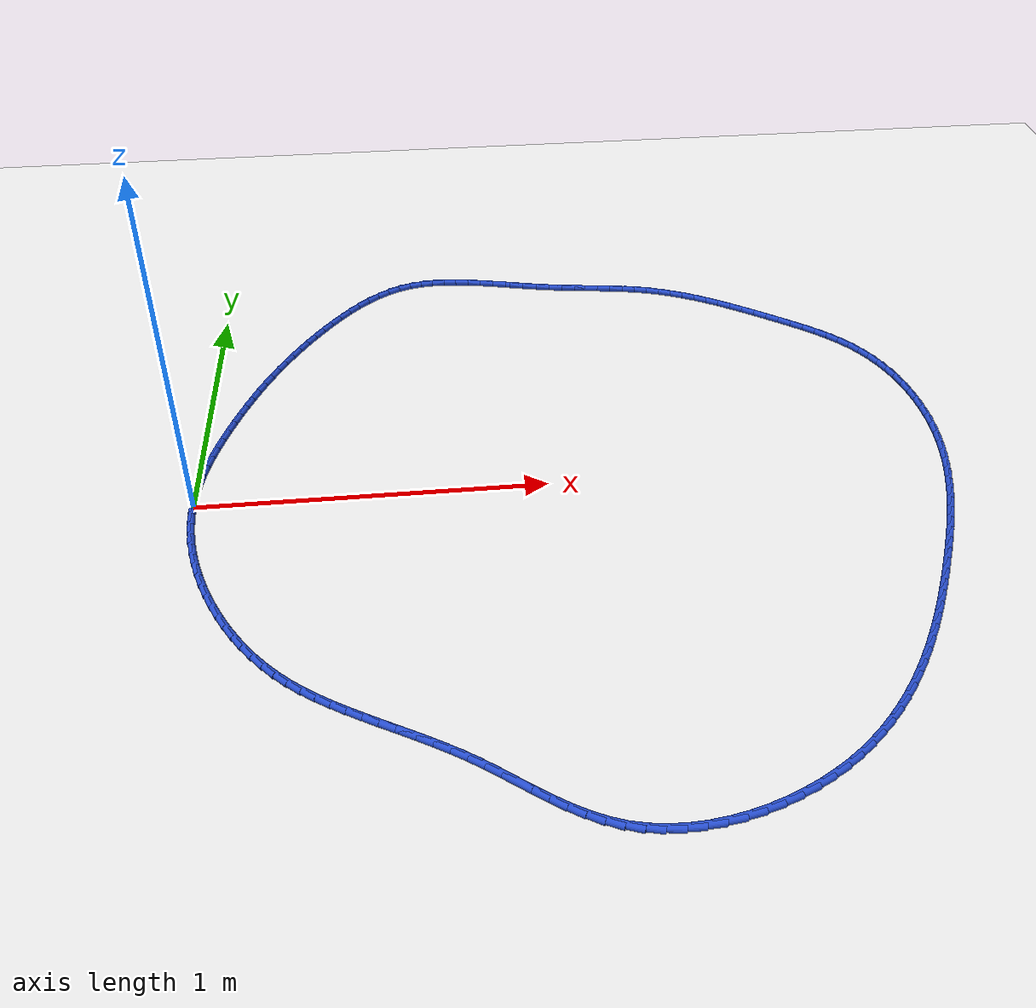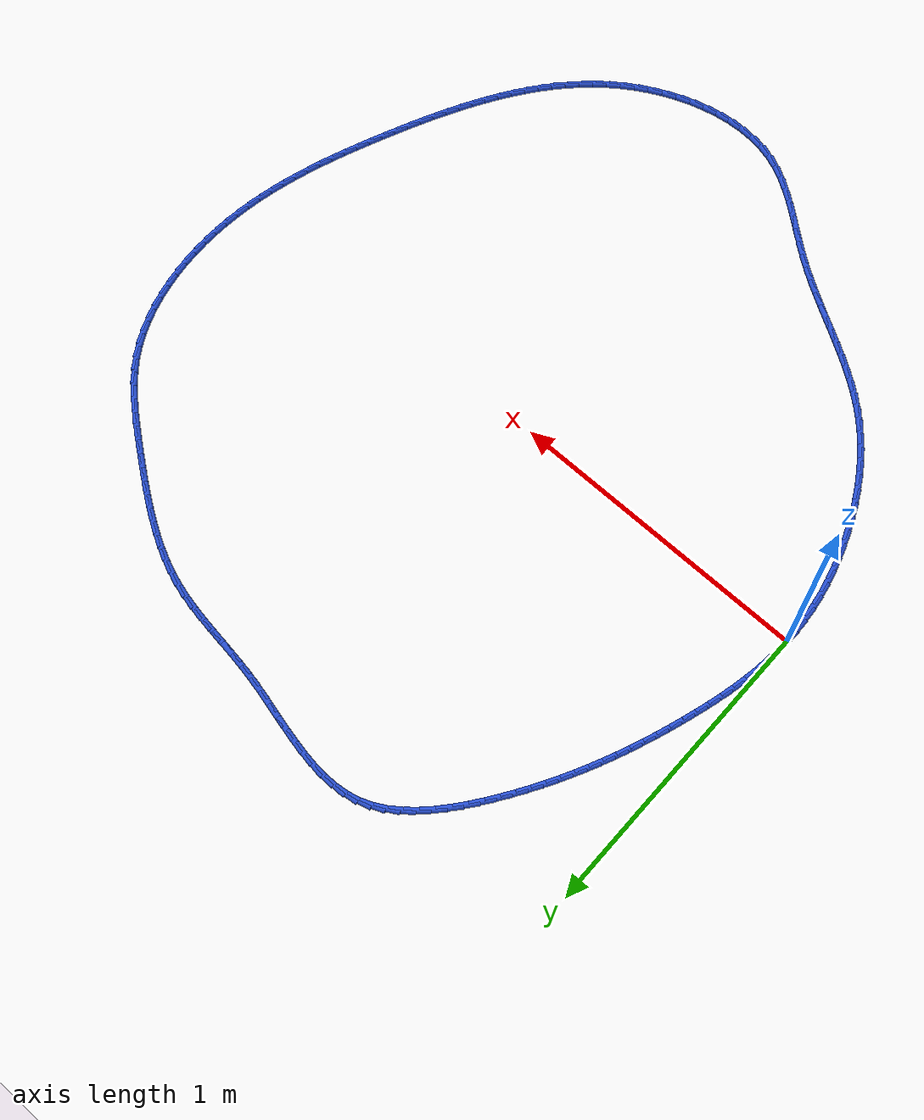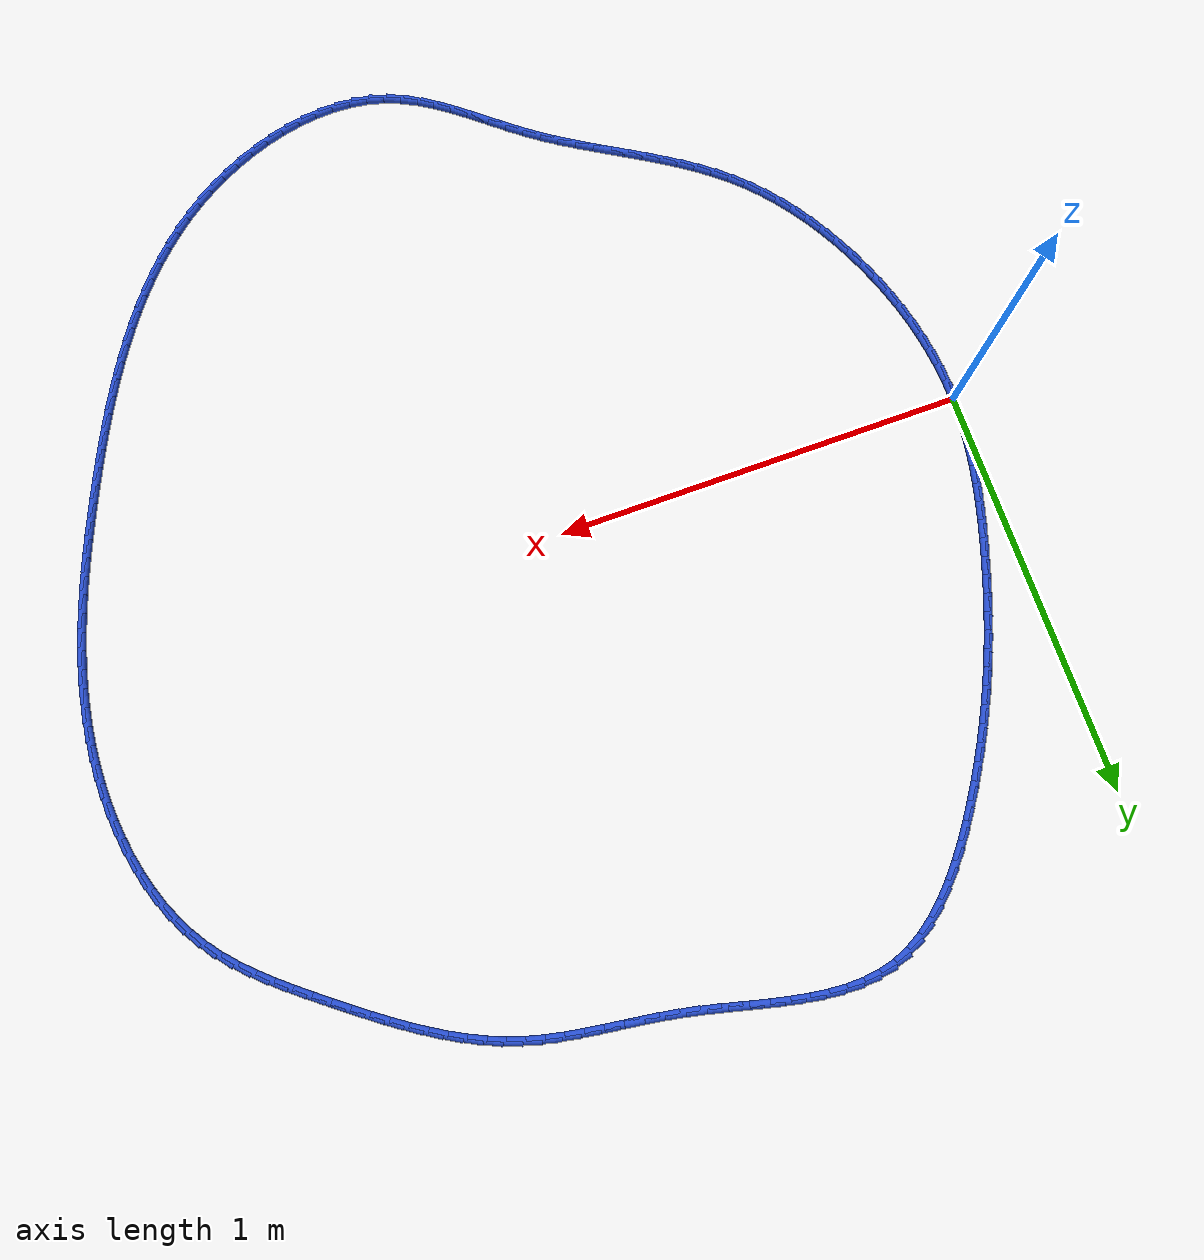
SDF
<sdf version="1.6">
 <world name="default">
  <light name="sun" type="directional">
   <pose>0 0 10 0 -0 0</pose>
   <diffuse>0.8 0.8 0.8 1</diffuse>
   <specular>0.2 0.2 0.2 1</specular>
   <attenuation>
    <range>1000</range>
    <constant>0.9</constant>
    <linear>0.01</linear>
    <quadratic>0.001</quadratic>
   </attenuation>
   <direction>-0.5 0.1 -0.9</direction>
  </light>
  <model name="ground_plane">
   <static>1</static>
   <link name="link">
    <collision name="collision">
     <geometry><plane><normal>0 0 1</normal><size>100 100</size></plane></geometry>
     <surface><friction><ode><mu>100</mu><mu2>50</mu2></ode></friction></surface>
    </collision>
    <visual name="visual">
     <cast_shadows>0</cast_shadows>
     <geometry><plane><normal>0 0 1</normal><size>100 100</size></plane></geometry>
     <material>
      <script><uri>file://media/materials/scripts/gazebo.material</uri><name>Gazebo/WhiteGlow</name></script>
     </material>
    </visual>
   </link>
  </model>
  <gravity>0 0 -9.8</gravity>
  <magnetic_field>6e-06 2.3e-05 -4.2e-05</magnetic_field>
  <atmosphere type="adiabatic"/>
  <physics name="default_physics" default="0" type="ode">
   <max_step_size>0.001</max_step_size>
   <real_time_factor>1</real_time_factor>
   <real_time_update_rate>1000</real_time_update_rate>
  </physics>
  <scene><ambient>0.4 0.4 0.4 1</ambient><background>0.7 0.7 0.7 1</background><shadows>1</shadows></scene>
  <spherical_coordinates>
   <surface_model>EARTH_WGS84</surface_model>
   <latitude_deg>0</latitude_deg>
   <longitude_deg>0</longitude_deg>
   <elevation>0</elevation>
   <heading_deg>0</heading_deg>
  </spherical_coordinates>
  <model name="line">
   <link name="link_0">
    <pose>1.0408340855860843e-17 1.3877787807814457e-17 0.01 0 1.57 1.5257420830498938</pose>
    <collision name="collision">
     <geometry><cylinder><radius>0.01</radius><length>0.08</length></cylinder></geometry>
    </collision>
    <visual name="visual">
     <material>
      <script><name>Gazebo/Blue</name><uri>file://media/materials/scripts/gazebo.material</uri></script>
     </material>
     <geometry><cylinder><radius>0.01</radius><length>0.08</length></cylinder></geometry>
    </visual>
   </link>
   <link name="link_1">
    <pose>0.001998602274265983 0.044329892466661275 0.01 0 1.57 1.4766051293833917</pose>
    <collision name="collision">
     <geometry><cylinder><radius>0.01</radius><length>0.08</length></cylinder></geometry>
    </collision>
    <visual name="visual">
     <material>
      <script><name>Gazebo/Blue</name><uri>file://media/materials/scripts/gazebo.material</uri></script>
     </material>
     <geometry><cylinder><radius>0.01</radius><length>0.08</length></cylinder></geometry>
    </visual>
   </link>
   <link name="link_2">
    <pose>0.006178565530487486 0.08857600605293878 0.01 0 1.57 1.4321764024368413</pose>
    <collision name="collision">
     <geometry><cylinder><radius>0.01</radius><length>0.08</length></cylinder></geometry>
    </collision>
    <visual name="visual">
     <material>
      <script><name>Gazebo/Blue</name><uri>file://media/materials/scripts/gazebo.material</uri></script>
     </material>
     <geometry><cylinder><radius>0.01</radius><length>0.08</length></cylinder></geometry>
    </visual>
   </link>
   <link name="link_3">
    <pose>0.012333009224333929 0.1326892381688568 0.01 0 1.57 1.3923854912597395</pose>
    <collision name="collision">
     <geometry><cylinder><radius>0.01</radius><length>0.08</length></cylinder></geometry>
    </collision>
    <visual name="visual">
     <material>
      <script><name>Gazebo/Blue</name><uri>file://media/materials/scripts/gazebo.material</uri></script>
     </material>
     <geometry><cylinder><radius>0.01</radius><length>0.08</length></cylinder></geometry>
    </visual>
   </link>
   <link name="link_4">
    <pose>0.02025505281147469 0.17662048622443965 0.01 0 1.57 1.357113080629409</pose>
    <collision name="collision">
     <geometry><cylinder><radius>0.01</radius><length>0.08</length></cylinder></geometry>
    </collision>
    <visual name="visual">
     <material>
      <script><name>Gazebo/Blue</name><uri>file://media/materials/scripts/gazebo.material</uri></script>
     </material>
     <geometry><cylinder><radius>0.01</radius><length>0.08</length></cylinder></geometry>
    </visual>
   </link>
   <link name="link_5">
    <pose>0.029737815747579173 0.22032064762971162 0.01 0 1.57 1.3262163553945956</pose>
    <collision name="collision">
     <geometry><cylinder><radius>0.01</radius><length>0.08</length></cylinder></geometry>
    </collision>
    <visual name="visual">
     <material>
      <script><name>Gazebo/Blue</name><uri>file://media/materials/scripts/gazebo.material</uri></script>
     </material>
     <geometry><cylinder><radius>0.01</radius><length>0.08</length></cylinder></geometry>
    </visual>
   </link>
   <link name="link_6">
    <pose>0.04057441748831677 0.2637406197946971 0.01 0 1.57 1.2995494605103628</pose>
    <collision name="collision">
     <geometry><cylinder><radius>0.01</radius><length>0.08</length></cylinder></geometry>
    </collision>
    <visual name="visual">
     <material>
      <script><name>Gazebo/Blue</name><uri>file://media/materials/scripts/gazebo.material</uri></script>
     </material>
     <geometry><cylinder><radius>0.01</radius><length>0.08</length></cylinder></geometry>
    </visual>
   </link>
   <link name="link_7">
    <pose>0.052557977489356845 0.30683130012942017 0.01 0 1.57 1.2769795149681797</pose>
    <collision name="collision">
     <geometry><cylinder><radius>0.01</radius><length>0.08</length></cylinder></geometry>
    </collision>
    <visual name="visual">
     <material>
      <script><name>Gazebo/Blue</name><uri>file://media/materials/scripts/gazebo.material</uri></script>
     </material>
     <geometry><cylinder><radius>0.01</radius><length>0.08</length></cylinder></geometry>
    </visual>
   </link>
   <link name="link_8">
    <pose>0.06548161520636885 0.3495435860439053 0.01 0 1.57 1.2583904293031734</pose>
    <collision name="collision">
     <geometry><cylinder><radius>0.01</radius><length>0.08</length></cylinder></geometry>
    </collision>
    <visual name="visual">
     <material>
      <script><name>Gazebo/Blue</name><uri>file://media/materials/scripts/gazebo.material</uri></script>
     </material>
     <geometry><cylinder><radius>0.01</radius><length>0.08</length></cylinder></geometry>
    </visual>
   </link>
   <link name="link_9">
    <pose>0.07913889944182109 0.3918285140394076 0.01 0 1.57 1.242228044069068</pose>
    <collision name="collision">
     <geometry><cylinder><radius>0.01</radius><length>0.08</length></cylinder></geometry>
    </collision>
    <visual name="visual">
     <material>
      <script><name>Gazebo/Blue</name><uri>file://media/materials/scripts/gazebo.material</uri></script>
     </material>
     <geometry><cylinder><radius>0.01</radius><length>0.08</length></cylinder></geometry>
    </visual>
   </link>
   <link name="link_10">
    <pose>0.09340069594287631 0.4336610471861761 0.01 0 1.57 1.2253391697142682</pose>
    <collision name="collision">
     <geometry><cylinder><radius>0.01</radius><length>0.08</length></cylinder></geometry>
    </collision>
    <visual name="visual">
     <material>
      <script><name>Gazebo/Blue</name><uri>file://media/materials/scripts/gazebo.material</uri></script>
     </material>
     <geometry><cylinder><radius>0.01</radius><length>0.08</length></cylinder></geometry>
    </visual>
   </link>
   <link name="link_11">
    <pose>0.10830224629352811 0.4750670296056615 0.01 0 1.57 1.2073701015631189</pose>
    <collision name="collision">
     <geometry><cylinder><radius>0.01</radius><length>0.08</length></cylinder></geometry>
    </collision>
    <visual name="visual">
     <material>
      <script><name>Gazebo/Blue</name><uri>file://media/materials/scripts/gazebo.material</uri></script>
     </material>
     <geometry><cylinder><radius>0.01</radius><length>0.08</length></cylinder></geometry>
    </visual>
   </link>
   <link name="link_12">
    <pose>0.12389983198406262 0.5160788181317066 0.01 0 1.57 1.1883844190177797</pose>
    <collision name="collision">
     <geometry><cylinder><radius>0.01</radius><length>0.08</length></cylinder></geometry>
    </collision>
    <visual name="visual">
     <material>
      <script><name>Gazebo/Blue</name><uri>file://media/materials/scripts/gazebo.material</uri></script>
     </material>
     <geometry><cylinder><radius>0.01</radius><length>0.08</length></cylinder></geometry>
    </visual>
   </link>
   <link name="link_13">
    <pose>0.14024973450476586 0.5567287695981534 0.01 0 1.57 1.1684573064323895</pose>
    <collision name="collision">
     <geometry><cylinder><radius>0.01</radius><length>0.08</length></cylinder></geometry>
    </collision>
    <visual name="visual">
     <material>
      <script><name>Gazebo/Blue</name><uri>file://media/materials/scripts/gazebo.material</uri></script>
     </material>
     <geometry><cylinder><radius>0.01</radius><length>0.08</length></cylinder></geometry>
    </visual>
   </link>
   <link name="link_14">
    <pose>0.15740823534592413 0.5970492408388449 0.01 0 1.57 1.1476749357797125</pose>
    <collision name="collision">
     <geometry><cylinder><radius>0.01</radius><length>0.08</length></cylinder></geometry>
    </collision>
    <visual name="visual">
     <material>
      <script><name>Gazebo/Blue</name><uri>file://media/materials/scripts/gazebo.material</uri></script>
     </material>
     <geometry><cylinder><radius>0.01</radius><length>0.08</length></cylinder></geometry>
    </visual>
   </link>
   <link name="link_15">
    <pose>0.17543161599782336 0.6370725886876232 0.01 0 1.57 1.1261334874155562</pose>
    <collision name="collision">
     <geometry><cylinder><radius>0.01</radius><length>0.08</length></cylinder></geometry>
    </collision>
    <visual name="visual">
     <material>
      <script><name>Gazebo/Blue</name><uri>file://media/materials/scripts/gazebo.material</uri></script>
     </material>
     <geometry><cylinder><radius>0.01</radius><length>0.08</length></cylinder></geometry>
    </visual>
   </link>
   <link name="link_16">
    <pose>0.19437615795074986 0.676831169978331 0.01 0 1.57 1.1039378161728166</pose>
    <collision name="collision">
     <geometry><cylinder><radius>0.01</radius><length>0.08</length></cylinder></geometry>
    </collision>
    <visual name="visual">
     <material>
      <script><name>Gazebo/Blue</name><uri>file://media/materials/scripts/gazebo.material</uri></script>
     </material>
     <geometry><cylinder><radius>0.01</radius><length>0.08</length></cylinder></geometry>
    </visual>
   </link>
   <link name="link_17">
    <pose>0.2142981426949896 0.7163573415448106 0.01 0 1.57 1.0811997932761765</pose>
    <collision name="collision">
     <geometry><cylinder><radius>0.01</radius><length>0.08</length></cylinder></geometry>
    </collision>
    <visual name="visual">
     <material>
      <script><name>Gazebo/Blue</name><uri>file://media/materials/scripts/gazebo.material</uri></script>
     </material>
     <geometry><cylinder><radius>0.01</radius><length>0.08</length></cylinder></geometry>
    </visual>
   </link>
   <link name="link_18">
    <pose>0.23525385172082863 0.7556834602209042 0.01 0 1.57 1.0580363778686888</pose>
    <collision name="collision">
     <geometry><cylinder><radius>0.01</radius><length>0.08</length></cylinder></geometry>
    </collision>
    <visual name="visual">
     <material>
      <script><name>Gazebo/Blue</name><uri>file://media/materials/scripts/gazebo.material</uri></script>
     </material>
     <geometry><cylinder><radius>0.01</radius><length>0.08</length></cylinder></geometry>
    </visual>
   </link>
   <link name="link_19">
    <pose>0.25729956651855335 0.7948418828404546 0.01 0 1.57 1.0345674927137507</pose>
    <collision name="collision">
     <geometry><cylinder><radius>0.01</radius><length>0.08</length></cylinder></geometry>
    </collision>
    <visual name="visual">
     <material>
      <script><name>Gazebo/Blue</name><uri>file://media/materials/scripts/gazebo.material</uri></script>
     </material>
     <geometry><cylinder><radius>0.01</radius><length>0.08</length></cylinder></geometry>
    </visual>
   </link>
   <link name="link_20">
    <pose>0.2804915685784496 0.8338649662373044 0.01 0 1.57 1.010913794378061</pose>
    <collision name="collision">
     <geometry><cylinder><radius>0.01</radius><length>0.08</length></cylinder></geometry>
    </collision>
    <visual name="visual">
     <material>
      <script><name>Gazebo/Blue</name><uri>file://media/materials/scripts/gazebo.material</uri></script>
     </material>
     <geometry><cylinder><radius>0.01</radius><length>0.08</length></cylinder></geometry>
    </visual>
   </link>
   <link name="link_21">
    <pose>0.3048861393908036 0.8727850672452957 0.01 0 1.57 0.9871944369028652</pose>
    <collision name="collision">
     <geometry><cylinder><radius>0.01</radius><length>0.08</length></cylinder></geometry>
    </collision>
    <visual name="visual">
     <material>
      <script><name>Gazebo/Blue</name><uri>file://media/materials/scripts/gazebo.material</uri></script>
     </material>
     <geometry><cylinder><radius>0.01</radius><length>0.08</length></cylinder></geometry>
    </visual>
   </link>
   <link name="link_22">
    <pose>0.3305395604459015 0.9116345426982708 0.01 0 1.57 0.9626043464974331</pose>
    <collision name="collision">
     <geometry><cylinder><radius>0.01</radius><length>0.08</length></cylinder></geometry>
    </collision>
    <visual name="visual">
     <material>
      <script><name>Gazebo/Blue</name><uri>file://media/materials/scripts/gazebo.material</uri></script>
     </material>
     <geometry><cylinder><radius>0.01</radius><length>0.08</length></cylinder></geometry>
    </visual>
   </link>
   <link name="link_23">
    <pose>0.3575045991326749 0.9503645577361717 0.01 0 1.57 0.931849075076979</pose>
    <collision name="collision">
     <geometry><cylinder><radius>0.01</radius><length>0.08</length></cylinder></geometry>
    </collision>
    <visual name="visual">
     <material>
      <script><name>Gazebo/Blue</name><uri>file://media/materials/scripts/gazebo.material</uri></script>
     </material>
     <geometry><cylinder><radius>0.01</radius><length>0.08</length></cylinder></geometry>
    </visual>
   </link>
   <link name="link_24">
    <pose>0.3858143244419218 0.9884711550792101 0.01 0 1.57 0.8923563930588253</pose>
    <collision name="collision">
     <geometry><cylinder><radius>0.01</radius><length>0.08</length></cylinder></geometry>
    </collision>
    <visual name="visual">
     <material>
      <script><name>Gazebo/Blue</name><uri>file://media/materials/scripts/gazebo.material</uri></script>
     </material>
     <geometry><cylinder><radius>0.01</radius><length>0.08</length></cylinder></geometry>
    </visual>
   </link>
   <link name="link_25">
    <pose>0.41549494590378233 1.0252918927672048 0.01 0 1.57 0.8428716413968468</pose>
    <collision name="collision">
     <geometry><cylinder><radius>0.01</radius><length>0.08</length></cylinder></geometry>
    </collision>
    <visual name="visual">
     <material>
      <script><name>Gazebo/Blue</name><uri>file://media/materials/scripts/gazebo.material</uri></script>
     </material>
     <geometry><cylinder><radius>0.01</radius><length>0.08</length></cylinder></geometry>
    </visual>
   </link>
   <link name="link_26">
    <pose>0.44657266606478274 1.0601641674867792 0.01 0 1.57 0.781695204537575</pose>
    <collision name="collision">
     <geometry><cylinder><radius>0.01</radius><length>0.08</length></cylinder></geometry>
    </collision>
    <visual name="visual">
     <material>
      <script><name>Gazebo/Blue</name><uri>file://media/materials/scripts/gazebo.material</uri></script>
     </material>
     <geometry><cylinder><radius>0.01</radius><length>0.08</length></cylinder></geometry>
    </visual>
   </link>
   <link name="link_27">
    <pose>0.47907368747144935 1.0924253759245597 0.01 0 1.57 0.7067059154107361</pose>
    <collision name="collision">
     <geometry><cylinder><radius>0.01</radius><length>0.08</length></cylinder></geometry>
    </collision>
    <visual name="visual">
     <material>
      <script><name>Gazebo/Blue</name><uri>file://media/materials/scripts/gazebo.material</uri></script>
     </material>
     <geometry><cylinder><radius>0.01</radius><length>0.08</length></cylinder></geometry>
    </visual>
   </link>
   <link name="link_28">
    <pose>0.5130242126703075 1.1214129147671688 0.01 0 1.57 0.6155011121087374</pose>
    <collision name="collision">
     <geometry><cylinder><radius>0.01</radius><length>0.08</length></cylinder></geometry>
    </collision>
    <visual name="visual">
     <material>
      <script><name>Gazebo/Blue</name><uri>file://media/materials/scripts/gazebo.material</uri></script>
     </material>
     <geometry><cylinder><radius>0.01</radius><length>0.08</length></cylinder></geometry>
    </visual>
   </link>
   <link name="link_29">
    <pose>0.5484504442078836 1.1464641807012315 0.01 0 1.57 0.505788853088822</pose>
    <collision name="collision">
     <geometry><cylinder><radius>0.01</radius><length>0.08</length></cylinder></geometry>
    </collision>
    <visual name="visual">
     <material>
      <script><name>Gazebo/Blue</name><uri>file://media/materials/scripts/gazebo.material</uri></script>
     </material>
     <geometry><cylinder><radius>0.01</radius><length>0.08</length></cylinder></geometry>
    </visual>
   </link>
   <link name="link_30">
    <pose>0.5853785846307036 1.1669165704133728 0.01 0 1.57 0.37621961756253836</pose>
    <collision name="collision">
     <geometry><cylinder><radius>0.01</radius><length>0.08</length></cylinder></geometry>
    </collision>
    <visual name="visual">
     <material>
      <script><name>Gazebo/Blue</name><uri>file://media/materials/scripts/gazebo.material</uri></script>
     </material>
     <geometry><cylinder><radius>0.01</radius><length>0.08</length></cylinder></geometry>
    </visual>
   </link>
   <link name="link_31">
    <pose>0.6238347421534952 1.1821081309257753 0.01 0 1.57 0.2358012511669368</pose>
    <collision name="collision">
     <geometry><cylinder><radius>0.01</radius><length>0.08</length></cylinder></geometry>
    </collision>
    <visual name="visual">
     <material>
      <script><name>Gazebo/Blue</name><uri>file://media/materials/scripts/gazebo.material</uri></script>
     </material>
     <geometry><cylinder><radius>0.01</radius><length>0.08</length></cylinder></geometry>
    </visual>
   </link>
   <link name="link_32">
    <pose>0.6637967330143256 1.191709840362082 0.01 0 1.57 0.10985685038646974</pose>
    <collision name="collision">
     <geometry><cylinder><radius>0.01</radius><length>0.08</length></cylinder></geometry>
    </collision>
    <visual name="visual">
     <material>
      <script><name>Gazebo/Blue</name><uri>file://media/materials/scripts/gazebo.material</uri></script>
     </material>
     <geometry><cylinder><radius>0.01</radius><length>0.08</length></cylinder></geometry>
    </visual>
   </link>
   <link name="link_33">
    <pose>0.7051155028430259 1.1962673391452363 0.01 0 1.57 0.00472501650289219</pose>
    <collision name="collision">
     <geometry><cylinder><radius>0.01</radius><length>0.08</length></cylinder></geometry>
    </collision>
    <visual name="visual">
     <material>
      <script><name>Gazebo/Blue</name><uri>file://media/materials/scripts/gazebo.material</uri></script>
     </material>
     <geometry><cylinder><radius>0.01</radius><length>0.08</length></cylinder></geometry>
    </visual>
   </link>
   <link name="link_34">
    <pose>0.7476214124975399 1.1964681817644827 0.01 0 1.57 -0.07951917519916012</pose>
    <collision name="collision">
     <geometry><cylinder><radius>0.01</radius><length>0.08</length></cylinder></geometry>
    </collision>
    <visual name="visual">
     <material>
      <script><name>Gazebo/Blue</name><uri>file://media/materials/scripts/gazebo.material</uri></script>
     </material>
     <geometry><cylinder><radius>0.01</radius><length>0.08</length></cylinder></geometry>
    </visual>
   </link>
   <link name="link_35">
    <pose>0.7911448228358118 1.1929999227090675 0.01 0 1.57 -0.14434894992813124</pose>
    <collision name="collision">
     <geometry><cylinder><radius>0.01</radius><length>0.08</length></cylinder></geometry>
    </collision>
    <visual name="visual">
     <material>
      <script><name>Gazebo/Blue</name><uri>file://media/materials/scripts/gazebo.material</uri></script>
     </material>
     <geometry><cylinder><radius>0.01</radius><length>0.08</length></cylinder></geometry>
    </visual>
   </link>
   <link name="link_36">
    <pose>0.8355160947157856 1.1865501164682357 0.01 0 1.57 -0.19170951329857033</pose>
    <collision name="collision">
     <geometry><cylinder><radius>0.01</radius><length>0.08</length></cylinder></geometry>
    </collision>
    <visual name="visual">
     <material>
      <script><name>Gazebo/Blue</name><uri>file://media/materials/scripts/gazebo.material</uri></script>
     </material>
     <geometry><cylinder><radius>0.01</radius><length>0.08</length></cylinder></geometry>
    </visual>
   </link>
   <link name="link_37">
    <pose>0.8805655889954055 1.177806317531233 0.01 0 1.57 -0.22339579641115231</pose>
    <collision name="collision">
     <geometry><cylinder><radius>0.01</radius><length>0.08</length></cylinder></geometry>
    </collision>
    <visual name="visual">
     <material>
      <script><name>Gazebo/Blue</name><uri>file://media/materials/scripts/gazebo.material</uri></script>
     </material>
     <geometry><cylinder><radius>0.01</radius><length>0.08</length></cylinder></geometry>
    </visual>
   </link>
   <link name="link_38">
    <pose>0.9261236665326155 1.1674560803873049 0.01 0 1.57 -0.2407677162134794</pose>
    <collision name="collision">
     <geometry><cylinder><radius>0.01</radius><length>0.08</length></cylinder></geometry>
    </collision>
    <visual name="visual">
     <material>
      <script><name>Gazebo/Blue</name><uri>file://media/materials/scripts/gazebo.material</uri></script>
     </material>
     <geometry><cylinder><radius>0.01</radius><length>0.08</length></cylinder></geometry>
    </visual>
   </link>
   <link name="link_39">
    <pose>0.9720206881853597 1.1561869595256966 0.01 0 1.57 -0.24464905357289662</pose>
    <collision name="collision">
     <geometry><cylinder><radius>0.01</radius><length>0.08</length></cylinder></geometry>
    </collision>
    <visual name="visual">
     <material>
      <script><name>Gazebo/Blue</name><uri>file://media/materials/scripts/gazebo.material</uri></script>
     </material>
     <geometry><cylinder><radius>0.01</radius><length>0.08</length></cylinder></geometry>
    </visual>
   </link>
   <link name="link_40">
    <pose>1.0180870148115813 1.1446865094356538 0.01 0 1.57 -0.23530659465012307</pose>
    <collision name="collision">
     <geometry><cylinder><radius>0.01</radius><length>0.08</length></cylinder></geometry>
    </collision>
    <visual name="visual">
     <material>
      <script><name>Gazebo/Blue</name><uri>file://media/materials/scripts/gazebo.material</uri></script>
     </material>
     <geometry><cylinder><radius>0.01</radius><length>0.08</length></cylinder></geometry>
    </visual>
   </link>
   <link name="link_41">
    <pose>1.064153007269226 1.1336422846064225 0.01 0 1.57 -0.2124591660073173</pose>
    <collision name="collision">
     <geometry><cylinder><radius>0.01</radius><length>0.08</length></cylinder></geometry>
    </collision>
    <visual name="visual">
     <material>
      <script><name>Gazebo/Blue</name><uri>file://media/materials/scripts/gazebo.material</uri></script>
     </material>
     <geometry><cylinder><radius>0.01</radius><length>0.08</length></cylinder></geometry>
    </visual>
   </link>
   <link name="link_42">
    <pose>1.110049026429621 1.123741839382333 0.01 0 1.57 -0.17975986718861003</pose>
    <collision name="collision">
     <geometry><cylinder><radius>0.01</radius><length>0.08</length></cylinder></geometry>
    </collision>
    <visual name="visual">
     <material>
      <script><name>Gazebo/Blue</name><uri>file://media/materials/scripts/gazebo.material</uri></script>
     </material>
     <geometry><cylinder><radius>0.01</radius><length>0.08</length></cylinder></geometry>
    </visual>
   </link>
   <link name="link_43">
    <pose>1.1556251099051444 1.1154596871540714 0.01 0 1.57 -0.15411755822495865</pose>
    <collision name="collision">
     <geometry><cylinder><radius>0.01</radius><length>0.08</length></cylinder></geometry>
    </collision>
    <visual name="visual">
     <material>
      <script><name>Gazebo/Blue</name><uri>file://media/materials/scripts/gazebo.material</uri></script>
     </material>
     <geometry><cylinder><radius>0.01</radius><length>0.08</length></cylinder></geometry>
    </visual>
   </link>
   <link name="link_44">
    <pose>1.2008079350905554 1.108440558967568 0.01 0 1.57 -0.14020257719143167</pose>
    <collision name="collision">
     <geometry><cylinder><radius>0.01</radius><length>0.08</length></cylinder></geometry>
    </collision>
    <visual name="visual">
     <material>
      <script><name>Gazebo/Blue</name><uri>file://media/materials/scripts/gazebo.material</uri></script>
     </material>
     <geometry><cylinder><radius>0.01</radius><length>0.08</length></cylinder></geometry>
    </visual>
   </link>
   <link name="link_45">
    <pose>1.2455428360337866 1.102127189452048 0.01 0 1.57 -0.13848285699634744</pose>
    <collision name="collision">
     <geometry><cylinder><radius>0.01</radius><length>0.08</length></cylinder></geometry>
    </collision>
    <visual name="visual">
     <material>
      <script><name>Gazebo/Blue</name><uri>file://media/materials/scripts/gazebo.material</uri></script>
     </material>
     <geometry><cylinder><radius>0.01</radius><length>0.08</length></cylinder></geometry>
    </visual>
   </link>
   <link name="link_46">
    <pose>1.289775146782773 1.0959623132367367 0.01 0 1.57 -0.1493912808206171</pose>
    <collision name="collision">
     <geometry><cylinder><radius>0.01</radius><length>0.08</length></cylinder></geometry>
    </collision>
    <visual name="visual">
     <material>
      <script><name>Gazebo/Blue</name><uri>file://media/materials/scripts/gazebo.material</uri></script>
     </material>
     <geometry><cylinder><radius>0.01</radius><length>0.08</length></cylinder></geometry>
    </visual>
   </link>
   <link name="link_47">
    <pose>1.3334502013854475 1.0893886649508593 0.01 0 1.57 -0.17332762516594027</pose>
    <collision name="collision">
     <geometry><cylinder><radius>0.01</radius><length>0.08</length></cylinder></geometry>
    </collision>
    <visual name="visual">
     <material>
      <script><name>Gazebo/Blue</name><uri>file://media/materials/scripts/gazebo.material</uri></script>
     </material>
     <geometry><cylinder><radius>0.01</radius><length>0.08</length></cylinder></geometry>
    </visual>
   </link>
   <link name="link_48">
    <pose>1.3765133338897453 1.0818489792236414 0.01 0 1.57 -0.21059748392331867</pose>
    <collision name="collision">
     <geometry><cylinder><radius>0.01</radius><length>0.08</length></cylinder></geometry>
    </collision>
    <visual name="visual">
     <material>
      <script><name>Gazebo/Blue</name><uri>file://media/materials/scripts/gazebo.material</uri></script>
     </material>
     <geometry><cylinder><radius>0.01</radius><length>0.08</length></cylinder></geometry>
    </visual>
   </link>
   <link name="link_49">
    <pose>1.4189098783435994 1.0727859906843082 0.01 0 1.57 -0.26127759936198397</pose>
    <collision name="collision">
     <geometry><cylinder><radius>0.01</radius><length>0.08</length></cylinder></geometry>
    </collision>
    <visual name="visual">
     <material>
      <script><name>Gazebo/Blue</name><uri>file://media/materials/scripts/gazebo.material</uri></script>
     </material>
     <geometry><cylinder><radius>0.01</radius><length>0.08</length></cylinder></geometry>
    </visual>
   </link>
   <link name="link_50">
    <pose>1.4605851687949447 1.0616424339620856 0.01 0 1.57 -0.32421507294622276</pose>
    <collision name="collision">
     <geometry><cylinder><radius>0.01</radius><length>0.08</length></cylinder></geometry>
    </collision>
    <visual name="visual">
     <material>
      <script><name>Gazebo/Blue</name><uri>file://media/materials/scripts/gazebo.material</uri></script>
     </material>
     <geometry><cylinder><radius>0.01</radius><length>0.08</length></cylinder></geometry>
    </visual>
   </link>
   <link name="link_51">
    <pose>1.5014892418000167 1.047895640811184 0.01 0 1.57 -0.3880398437940959</pose>
    <collision name="collision">
     <geometry><cylinder><radius>0.01</radius><length>0.08</length></cylinder></geometry>
    </collision>
    <visual name="visual">
     <material>
      <script><name>Gazebo/Blue</name><uri>file://media/materials/scripts/gazebo.material</uri></script>
     </material>
     <geometry><cylinder><radius>0.01</radius><length>0.08</length></cylinder></geometry>
    </visual>
   </link>
   <link name="link_52">
    <pose>1.541634998041206 1.0314854446742712 0.01 0 1.57 -0.4448444985155367</pose>
    <collision name="collision">
     <geometry><cylinder><radius>0.01</radius><length>0.08</length></cylinder></geometry>
    </collision>
    <visual name="visual">
     <material>
      <script><name>Gazebo/Blue</name><uri>file://media/materials/scripts/gazebo.material</uri></script>
     </material>
     <geometry><cylinder><radius>0.01</radius><length>0.08</length></cylinder></geometry>
    </visual>
   </link>
   <link name="link_53">
    <pose>1.5810801612970582 1.012681449865274 0.01 0 1.57 -0.4944812647800226</pose>
    <collision name="collision">
     <geometry><cylinder><radius>0.01</radius><length>0.08</length></cylinder></geometry>
    </collision>
    <visual name="visual">
     <material>
      <script><name>Gazebo/Blue</name><uri>file://media/materials/scripts/gazebo.material</uri></script>
     </material>
     <geometry><cylinder><radius>0.01</radius><length>0.08</length></cylinder></geometry>
    </visual>
   </link>
   <link name="link_54">
    <pose>1.6198834197357146 0.9917603558705911 0.01 0 1.57 -0.5371322830194737</pose>
    <collision name="collision">
     <geometry><cylinder><radius>0.01</radius><length>0.08</length></cylinder></geometry>
    </collision>
    <visual name="visual">
     <material>
      <script><name>Gazebo/Blue</name><uri>file://media/materials/scripts/gazebo.material</uri></script>
     </material>
     <geometry><cylinder><radius>0.01</radius><length>0.08</length></cylinder></geometry>
    </visual>
   </link>
   <link name="link_55">
    <pose>1.658103461525318 0.96899886217662 0.01 0 1.57 -0.573069307996929</pose>
    <collision name="collision">
     <geometry><cylinder><radius>0.01</radius><length>0.08</length></cylinder></geometry>
    </collision>
    <visual name="visual">
     <material>
      <script><name>Gazebo/Blue</name><uri>file://media/materials/scripts/gazebo.material</uri></script>
     </material>
     <geometry><cylinder><radius>0.01</radius><length>0.08</length></cylinder></geometry>
    </visual>
   </link>
   <link name="link_56">
    <pose>1.695798974834011 0.9446736682697583 0.01 0 1.57 -0.6025936014822144</pose>
    <collision name="collision">
     <geometry><cylinder><radius>0.01</radius><length>0.08</length></cylinder></geometry>
    </collision>
    <visual name="visual">
     <material>
      <script><name>Gazebo/Blue</name><uri>file://media/materials/scripts/gazebo.material</uri></script>
     </material>
     <geometry><cylinder><radius>0.01</radius><length>0.08</length></cylinder></geometry>
    </visual>
   </link>
   <link name="link_57">
    <pose>1.7330286478299357 0.9190614736364052 0.01 0 1.57 -0.6259926779803051</pose>
    <collision name="collision">
     <geometry><cylinder><radius>0.01</radius><length>0.08</length></cylinder></geometry>
    </collision>
    <visual name="visual">
     <material>
      <script><name>Gazebo/Blue</name><uri>file://media/materials/scripts/gazebo.material</uri></script>
     </material>
     <geometry><cylinder><radius>0.01</radius><length>0.08</length></cylinder></geometry>
    </visual>
   </link>
   <link name="link_58">
    <pose>1.769851168681235 0.8924389777629576 0.01 0 1.57 -0.6435108466424923</pose>
    <collision name="collision">
     <geometry><cylinder><radius>0.01</radius><length>0.08</length></cylinder></geometry>
    </collision>
    <visual name="visual">
     <material>
      <script><name>Gazebo/Blue</name><uri>file://media/materials/scripts/gazebo.material</uri></script>
     </material>
     <geometry><cylinder><radius>0.01</radius><length>0.08</length></cylinder></geometry>
    </visual>
   </link>
   <link name="link_59">
    <pose>1.806325225556051 0.8650828801358146 0.01 0 1.57 -0.6553298244499957</pose>
    <collision name="collision">
     <geometry><cylinder><radius>0.01</radius><length>0.08</length></cylinder></geometry>
    </collision>
    <visual name="visual">
     <material>
      <script><name>Gazebo/Blue</name><uri>file://media/materials/scripts/gazebo.material</uri></script>
     </material>
     <geometry><cylinder><radius>0.01</radius><length>0.08</length></cylinder></geometry>
    </visual>
   </link>
   <link name="link_60">
    <pose>1.8425095066225263 0.8372698802413738 0.01 0 1.57 -0.6620347036509198</pose>
    <collision name="collision">
     <geometry><cylinder><radius>0.01</radius><length>0.08</length></cylinder></geometry>
    </collision>
    <visual name="visual">
     <material>
      <script><name>Gazebo/Blue</name><uri>file://media/materials/scripts/gazebo.material</uri></script>
     </material>
     <geometry><cylinder><radius>0.01</radius><length>0.08</length></cylinder></geometry>
    </visual>
   </link>
   <link name="link_61">
    <pose>1.8784491580475853 0.8092595812209517 0.01 0 1.57 -0.6724374659433364</pose>
    <collision name="collision">
     <geometry><cylinder><radius>0.01</radius><length>0.08</length></cylinder></geometry>
    </collision>
    <visual name="visual">
     <material>
      <script><name>Gazebo/Blue</name><uri>file://media/materials/scripts/gazebo.material</uri></script>
     </material>
     <geometry><cylinder><radius>0.01</radius><length>0.08</length></cylinder></geometry>
    </visual>
   </link>
   <link name="link_62">
    <pose>1.9139419016815755 0.7809992208992862 0.01 0 1.57 -0.6944023319127265</pose>
    <collision name="collision">
     <geometry><cylinder><radius>0.01</radius><length>0.08</length></cylinder></geometry>
    </collision>
    <visual name="visual">
     <material>
      <script><name>Gazebo/Blue</name><uri>file://media/materials/scripts/gazebo.material</uri></script>
     </material>
     <geometry><cylinder><radius>0.01</radius><length>0.08</length></cylinder></geometry>
    </visual>
   </link>
   <link name="link_63">
    <pose>1.9485691179694276 0.7521629129695494 0.01 0 1.57 -0.7285751931079465</pose>
    <collision name="collision">
     <geometry><cylinder><radius>0.01</radius><length>0.08</length></cylinder></geometry>
    </collision>
    <visual name="visual">
     <material>
      <script><name>Gazebo/Blue</name><uri>file://media/materials/scripts/gazebo.material</uri></script>
     </material>
     <geometry><cylinder><radius>0.01</radius><length>0.08</length></cylinder></geometry>
    </visual>
   </link>
   <link name="link_64">
    <pose>1.981904897079331 0.7224155673828034 0.01 0 1.57 -0.7754170256258487</pose>
    <collision name="collision">
     <geometry><cylinder><radius>0.01</radius><length>0.08</length></cylinder></geometry>
    </collision>
    <visual name="visual">
     <material>
      <script><name>Gazebo/Blue</name><uri>file://media/materials/scripts/gazebo.material</uri></script>
     </material>
     <geometry><cylinder><radius>0.01</radius><length>0.08</length></cylinder></geometry>
    </visual>
   </link>
   <link name="link_65">
    <pose>2.013523329179477 0.6914220940901102 0.01 0 1.57 -0.835308692647815</pose>
    <collision name="collision">
     <geometry><cylinder><radius>0.01</radius><length>0.08</length></cylinder></geometry>
    </collision>
    <visual name="visual">
     <material>
      <script><name>Gazebo/Blue</name><uri>file://media/materials/scripts/gazebo.material</uri></script>
     </material>
     <geometry><cylinder><radius>0.01</radius><length>0.08</length></cylinder></geometry>
    </visual>
   </link>
   <link name="link_66">
    <pose>2.0429985044380565 0.6588474030425313 0.01 0 1.57 -0.9083154257611132</pose>
    <collision name="collision">
     <geometry><cylinder><radius>0.01</radius><length>0.08</length></cylinder></geometry>
    </collision>
    <visual name="visual">
     <material>
      <script><name>Gazebo/Blue</name><uri>file://media/materials/scripts/gazebo.material</uri></script>
     </material>
     <geometry><cylinder><radius>0.01</radius><length>0.08</length></cylinder></geometry>
    </visual>
   </link>
   <link name="link_67">
    <pose>2.0699045130232587 0.6243564041911289 0.01 0 1.57 -0.9915361157523247</pose>
    <collision name="collision">
     <geometry><cylinder><radius>0.01</radius><length>0.08</length></cylinder></geometry>
    </collision>
    <visual name="visual">
     <material>
      <script><name>Gazebo/Blue</name><uri>file://media/materials/scripts/gazebo.material</uri></script>
     </material>
     <geometry><cylinder><radius>0.01</radius><length>0.08</length></cylinder></geometry>
    </visual>
   </link>
   <link name="link_68">
    <pose>2.093886207290143 0.5876934043130307 0.01 0 1.57 -1.0726686446524845</pose>
    <collision name="collision">
     <geometry><cylinder><radius>0.01</radius><length>0.08</length></cylinder></geometry>
    </collision>
    <visual name="visual">
     <material>
      <script><name>Gazebo/Blue</name><uri>file://media/materials/scripts/gazebo.material</uri></script>
     </material>
     <geometry><cylinder><radius>0.01</radius><length>0.08</length></cylinder></geometry>
    </visual>
   </link>
   <link name="link_69">
    <pose>2.114935080435692 0.548991649304567 0.01 0 1.57 -1.1480705612795197</pose>
    <collision name="collision">
     <geometry><cylinder><radius>0.01</radius><length>0.08</length></cylinder></geometry>
    </collision>
    <visual name="visual">
     <material>
      <script><name>Gazebo/Blue</name><uri>file://media/materials/scripts/gazebo.material</uri></script>
     </material>
     <geometry><cylinder><radius>0.01</radius><length>0.08</length></cylinder></geometry>
    </visual>
   </link>
   <link name="link_70">
    <pose>2.1331486015663956 0.5085032925072305 0.01 0 1.57 -1.217940256252661</pose>
    <collision name="collision">
     <geometry><cylinder><radius>0.01</radius><length>0.08</length></cylinder></geometry>
    </collision>
    <visual name="visual">
     <material>
      <script><name>Gazebo/Blue</name><uri>file://media/materials/scripts/gazebo.material</uri></script>
     </material>
     <geometry><cylinder><radius>0.01</radius><length>0.08</length></cylinder></geometry>
    </visual>
   </link>
   <link name="link_71">
    <pose>2.1486242664745983 0.4664805172046598 0.01 0 1.57 -1.28265193003333</pose>
    <collision name="collision">
     <geometry><cylinder><radius>0.01</radius><length>0.08</length></cylinder></geometry>
    </collision>
    <visual name="visual">
     <material>
      <script><name>Gazebo/Blue</name><uri>file://media/materials/scripts/gazebo.material</uri></script>
     </material>
     <geometry><cylinder><radius>0.01</radius><length>0.08</length></cylinder></geometry>
    </visual>
   </link>
   <link name="link_72">
    <pose>2.161459570952641 0.4231755066804945 0.01 0 1.57 -1.3426857418835236</pose>
    <collision name="collision">
     <geometry><cylinder><radius>0.01</radius><length>0.08</length></cylinder></geometry>
    </collision>
    <visual name="visual">
     <material>
      <script><name>Gazebo/Blue</name><uri>file://media/materials/scripts/gazebo.material</uri></script>
     </material>
     <geometry><cylinder><radius>0.01</radius><length>0.08</length></cylinder></geometry>
    </visual>
   </link>
   <link name="link_73">
    <pose>2.1717520107928663 0.37884044421837276 0.01 0 1.57 -1.3985765984955845</pose>
    <collision name="collision">
     <geometry><cylinder><radius>0.01</radius><length>0.08</length></cylinder></geometry>
    </collision>
    <visual name="visual">
     <material>
      <script><name>Gazebo/Blue</name><uri>file://media/materials/scripts/gazebo.material</uri></script>
     </material>
     <geometry><cylinder><radius>0.01</radius><length>0.08</length></cylinder></geometry>
    </visual>
   </link>
   <link name="link_74">
    <pose>2.1795990817876154 0.33372751310193394 0.01 0 1.57 -1.4508800426221542</pose>
    <collision name="collision">
     <geometry><cylinder><radius>0.01</radius><length>0.08</length></cylinder></geometry>
    </collision>
    <visual name="visual">
     <material>
      <script><name>Gazebo/Blue</name><uri>file://media/materials/scripts/gazebo.material</uri></script>
     </material>
     <geometry><cylinder><radius>0.01</radius><length>0.08</length></cylinder></geometry>
    </visual>
   </link>
   <link name="link_75">
    <pose>2.1850982797292318 0.28808889661481685 0.01 0 1.57 -1.5001523553809544</pose>
    <collision name="collision">
     <geometry><cylinder><radius>0.01</radius><length>0.08</length></cylinder></geometry>
    </collision>
    <visual name="visual">
     <material>
      <script><name>Gazebo/Blue</name><uri>file://media/materials/scripts/gazebo.material</uri></script>
     </material>
     <geometry><cylinder><radius>0.01</radius><length>0.08</length></cylinder></geometry>
    </visual>
   </link>
   <link name="link_76">
    <pose>2.1883471004100556 0.24217677804065954 0.01 0 1.57 -1.5469415624723986</pose>
    <collision name="collision">
     <geometry><cylinder><radius>0.01</radius><length>0.08</length></cylinder></geometry>
    </collision>
    <visual name="visual">
     <material>
      <script><name>Gazebo/Blue</name><uri>file://media/materials/scripts/gazebo.material</uri></script>
     </material>
     <geometry><cylinder><radius>0.01</radius><length>0.08</length></cylinder></geometry>
    </visual>
   </link>
   <link name="link_77">
    <pose>2.189443039622429 0.1962433406631018 0.01 0 1.57 1.5498061397692606</pose>
    <collision name="collision">
     <geometry><cylinder><radius>0.01</radius><length>0.08</length></cylinder></geometry>
    </collision>
    <visual name="visual">
     <material>
      <script><name>Gazebo/Blue</name><uri>file://media/materials/scripts/gazebo.material</uri></script>
     </material>
     <geometry><cylinder><radius>0.01</radius><length>0.08</length></cylinder></geometry>
    </visual>
   </link>
   <link name="link_78">
    <pose>2.188483593158755 0.1505407677649784 0.01 0 1.57 1.5065107761619543</pose>
    <collision name="collision">
     <geometry><cylinder><radius>0.01</radius><length>0.08</length></cylinder></geometry>
    </collision>
    <visual name="visual">
     <material>
      <script><name>Gazebo/Blue</name><uri>file://media/materials/scripts/gazebo.material</uri></script>
     </material>
     <geometry><cylinder><radius>0.01</radius><length>0.08</length></cylinder></geometry>
    </visual>
   </link>
   <link name="link_79">
    <pose>2.1855696616737297 0.10527528771269447 0.01 0 1.57 1.4650864999947142</pose>
    <collision name="collision">
     <geometry><cylinder><radius>0.01</radius><length>0.08</length></cylinder></geometry>
    </collision>
    <visual name="visual">
     <material>
      <script><name>Gazebo/Blue</name><uri>file://media/materials/scripts/gazebo.material</uri></script>
     </material>
     <geometry><cylinder><radius>0.01</radius><length>0.08</length></cylinder></geometry>
    </visual>
   </link>
   <link name="link_80">
    <pose>2.1808156593665586 0.06047073858650981 0.01 0 1.57 1.4258424098330205</pose>
    <collision name="collision">
     <geometry><cylinder><radius>0.01</radius><length>0.08</length></cylinder></geometry>
    </collision>
    <visual name="visual">
     <material>
      <script><name>Gazebo/Blue</name><uri>file://media/materials/scripts/gazebo.material</uri></script>
     </material>
     <geometry><cylinder><radius>0.01</radius><length>0.08</length></cylinder></geometry>
    </visual>
   </link>
   <link name="link_81">
    <pose>2.174339352551957 0.01610571546569134 0.01 0 1.57 1.3889501642694382</pose>
    <collision name="collision">
     <geometry><cylinder><radius>0.01</radius><length>0.08</length></cylinder></geometry>
    </collision>
    <visual name="visual">
     <material>
      <script><name>Gazebo/Blue</name><uri>file://media/materials/scripts/gazebo.material</uri></script>
     </material>
     <geometry><cylinder><radius>0.01</radius><length>0.08</length></cylinder></geometry>
    </visual>
   </link>
   <link name="link_82">
    <pose>2.1662585075446428 -0.02784118657049474 0.01 0 1.57 1.3545400528799303</pose>
    <collision name="collision">
     <geometry><cylinder><radius>0.01</radius><length>0.08</length></cylinder></geometry>
    </collision>
    <visual name="visual">
     <material>
      <script><name>Gazebo/Blue</name><uri>file://media/materials/scripts/gazebo.material</uri></script>
     </material>
     <geometry><cylinder><radius>0.01</radius><length>0.08</length></cylinder></geometry>
    </visual>
   </link>
   <link name="link_83">
    <pose>2.156690890659331 -0.07139137244277999 0.01 0 1.57 1.322704913757637</pose>
    <collision name="collision">
     <geometry><cylinder><radius>0.01</radius><length>0.08</length></cylinder></geometry>
    </collision>
    <visual name="visual">
     <material>
      <script><name>Gazebo/Blue</name><uri>file://media/materials/scripts/gazebo.material</uri></script>
     </material>
     <geometry><cylinder><radius>0.01</radius><length>0.08</length></cylinder></geometry>
    </visual>
   </link>
   <link name="link_84">
    <pose>2.1457542682107396 -0.11456624707189816 0.01 0 1.57 1.2935052513373297</pose>
    <collision name="collision">
     <geometry><cylinder><radius>0.01</radius><length>0.08</length></cylinder></geometry>
    </collision>
    <visual name="visual">
     <material>
      <script><name>Gazebo/Blue</name><uri>file://media/materials/scripts/gazebo.material</uri></script>
     </material>
     <geometry><cylinder><radius>0.01</radius><length>0.08</length></cylinder></geometry>
    </visual>
   </link>
   <link name="link_85">
    <pose>2.1335664065135855 -0.15738721537858238 0.01 0 1.57 1.2669749650793514</pose>
    <collision name="collision">
     <geometry><cylinder><radius>0.01</radius><length>0.08</length></cylinder></geometry>
    </collision>
    <visual name="visual">
     <material>
      <script><name>Gazebo/Blue</name><uri>file://media/materials/scripts/gazebo.material</uri></script>
     </material>
     <geometry><cylinder><radius>0.01</radius><length>0.08</length></cylinder></geometry>
    </visual>
   </link>
   <link name="link_86">
    <pose>2.120245071882583 -0.19987568228356556 0.01 0 1.57 1.2431272048756725</pose>
    <collision name="collision">
     <geometry><cylinder><radius>0.01</radius><length>0.08</length></cylinder></geometry>
    </collision>
    <visual name="visual">
     <material>
      <script><name>Gazebo/Blue</name><uri>file://media/materials/scripts/gazebo.material</uri></script>
     </material>
     <geometry><cylinder><radius>0.01</radius><length>0.08</length></cylinder></geometry>
    </visual>
   </link>
   <link name="link_87">
    <pose>2.1059080306324516 -0.24205305270758168 0.01 0 1.57 1.2219599957089848</pose>
    <collision name="collision">
     <geometry><cylinder><radius>0.01</radius><length>0.08</length></cylinder></geometry>
    </collision>
    <visual name="visual">
     <material>
      <script><name>Gazebo/Blue</name><uri>file://media/materials/scripts/gazebo.material</uri></script>
     </material>
     <geometry><cylinder><radius>0.01</radius><length>0.08</length></cylinder></geometry>
    </visual>
   </link>
   <link name="link_88">
    <pose>2.0906730490779064 -0.2839407315713621 0.01 0 1.57 1.203461397400954</pose>
    <collision name="collision">
     <geometry><cylinder><radius>0.01</radius><length>0.08</length></cylinder></geometry>
    </collision>
    <visual name="visual">
     <material>
      <script><name>Gazebo/Blue</name><uri>file://media/materials/scripts/gazebo.material</uri></script>
     </material>
     <geometry><cylinder><radius>0.01</radius><length>0.08</length></cylinder></geometry>
    </visual>
   </link>
   <link name="link_89">
    <pose>2.0746578935336646 -0.3255601237956408 0.01 0 1.57 1.1876140702316524</pose>
    <collision name="collision">
     <geometry><cylinder><radius>0.01</radius><length>0.08</length></cylinder></geometry>
    </collision>
    <visual name="visual">
     <material>
      <script><name>Gazebo/Blue</name><uri>file://media/materials/scripts/gazebo.material</uri></script>
     </material>
     <geometry><cylinder><radius>0.01</radius><length>0.08</length></cylinder></geometry>
    </visual>
   </link>
   <link name="link_90">
    <pose>2.057980330314442 -0.36693263430115075 0.01 0 1.57 1.1743991973009729</pose>
    <collision name="collision">
     <geometry><cylinder><radius>0.01</radius><length>0.08</length></cylinder></geometry>
    </collision>
    <visual name="visual">
     <material>
      <script><name>Gazebo/Blue</name><uri>file://media/materials/scripts/gazebo.material</uri></script>
     </material>
     <geometry><cylinder><radius>0.01</radius><length>0.08</length></cylinder></geometry>
    </visual>
   </link>
   <link name="link_91">
    <pose>2.0407581257349565 -0.40807966800862494 0.01 0 1.57 1.1637997670919964</pose>
    <collision name="collision">
     <geometry><cylinder><radius>0.01</radius><length>0.08</length></cylinder></geometry>
    </collision>
    <visual name="visual">
     <material>
      <script><name>Gazebo/Blue</name><uri>file://media/materials/scripts/gazebo.material</uri></script>
     </material>
     <geometry><cylinder><radius>0.01</radius><length>0.08</length></cylinder></geometry>
    </visual>
   </link>
   <link name="link_92">
    <pose>2.023109046019623 -0.44902262981094 0.01 0 1.57 1.1549796135763377</pose>
    <collision name="collision">
     <geometry><cylinder><radius>0.01</radius><length>0.08</length></cylinder></geometry>
    </collision>
    <visual name="visual">
     <material>
      <script><name>Gazebo/Blue</name><uri>file://media/materials/scripts/gazebo.material</uri></script>
     </material>
     <geometry><cylinder><radius>0.01</radius><length>0.08</length></cylinder></geometry>
    </visual>
   </link>
   <link name="link_93">
    <pose>2.0051155618706558 -0.4897720361724187 0.01 0 1.57 1.1447706381986502</pose>
    <collision name="collision">
     <geometry><cylinder><radius>0.01</radius><length>0.08</length></cylinder></geometry>
    </collision>
    <visual name="visual">
     <material>
      <script><name>Gazebo/Blue</name><uri>file://media/materials/scripts/gazebo.material</uri></script>
     </material>
     <geometry><cylinder><radius>0.01</radius><length>0.08</length></cylinder></geometry>
    </visual>
   </link>
   <link name="link_94">
    <pose>1.9867247132834671 -0.5302966241054129 0.01 0 1.57 1.1324091604863993</pose>
    <collision name="collision">
     <geometry><cylinder><radius>0.01</radius><length>0.08</length></cylinder></geometry>
    </collision>
    <visual name="visual">
     <material>
      <script><name>Gazebo/Blue</name><uri>file://media/materials/scripts/gazebo.material</uri></script>
     </material>
     <geometry><cylinder><radius>0.01</radius><length>0.08</length></cylinder></geometry>
    </visual>
   </link>
   <link name="link_95">
    <pose>1.9678510623096768 -0.5705551113974986 0.01 0 1.57 1.1178919904817513</pose>
    <collision name="collision">
     <geometry><cylinder><radius>0.01</radius><length>0.08</length></cylinder></geometry>
    </collision>
    <visual name="visual">
     <material>
      <script><name>Gazebo/Blue</name><uri>file://media/materials/scripts/gazebo.material</uri></script>
     </material>
     <geometry><cylinder><radius>0.01</radius><length>0.08</length></cylinder></geometry>
    </visual>
   </link>
   <link name="link_96">
    <pose>1.9484091710009055 -0.6105062158362525 0.01 0 1.57 1.1012203164192498</pose>
    <collision name="collision">
     <geometry><cylinder><radius>0.01</radius><length>0.08</length></cylinder></geometry>
    </collision>
    <visual name="visual">
     <material>
      <script><name>Gazebo/Blue</name><uri>file://media/materials/scripts/gazebo.material</uri></script>
     </material>
     <geometry><cylinder><radius>0.01</radius><length>0.08</length></cylinder></geometry>
    </visual>
   </link>
   <link name="link_97">
    <pose>1.9283136014087723 -0.6501086552092494 0.01 0 1.57 1.082401728507617</pose>
    <collision name="collision">
     <geometry><cylinder><radius>0.01</radius><length>0.08</length></cylinder></geometry>
    </collision>
    <visual name="visual">
     <material>
      <script><name>Gazebo/Blue</name><uri>file://media/materials/scripts/gazebo.material</uri></script>
     </material>
     <geometry><cylinder><radius>0.01</radius><length>0.08</length></cylinder></geometry>
    </visual>
   </link>
   <link name="link_98">
    <pose>1.9074789155848977 -0.6893211473040662 0.01 0 1.57 1.061452505541421</pose>
    <collision name="collision">
     <geometry><cylinder><radius>0.01</radius><length>0.08</length></cylinder></geometry>
    </collision>
    <visual name="visual">
     <material>
      <script><name>Gazebo/Blue</name><uri>file://media/materials/scripts/gazebo.material</uri></script>
     </material>
     <geometry><cylinder><radius>0.01</radius><length>0.08</length></cylinder></geometry>
    </visual>
   </link>
   <link name="link_99">
    <pose>1.8858196755809022 -0.7281024099082791 0.01 0 1.57 1.0383853793921216</pose>
    <collision name="collision">
     <geometry><cylinder><radius>0.01</radius><length>0.08</length></cylinder></geometry>
    </collision>
    <visual name="visual">
     <material>
      <script><name>Gazebo/Blue</name><uri>file://media/materials/scripts/gazebo.material</uri></script>
     </material>
     <geometry><cylinder><radius>0.01</radius><length>0.08</length></cylinder></geometry>
    </visual>
   </link>
   <link name="link_100">
    <pose>1.8632503416403992 -0.7664100434904361 0.01 0 1.57 1.0127249083158532</pose>
    <collision name="collision">
     <geometry><cylinder><radius>0.01</radius><length>0.08</length></cylinder></geometry>
    </collision>
    <visual name="visual">
     <material>
      <script><name>Gazebo/Blue</name><uri>file://media/materials/scripts/gazebo.material</uri></script>
     </material>
     <geometry><cylinder><radius>0.01</radius><length>0.08</length></cylinder></geometry>
    </visual>
   </link>
   <link name="link_101">
    <pose>1.8396819284599766 -0.8041638344472414 0.01 0 1.57 0.9838230003383691</pose>
    <collision name="collision">
     <geometry><cylinder><radius>0.01</radius><length>0.08</length></cylinder></geometry>
    </collision>
    <visual name="visual">
     <material>
      <script><name>Gazebo/Blue</name><uri>file://media/materials/scripts/gazebo.material</uri></script>
     </material>
     <geometry><cylinder><radius>0.01</radius><length>0.08</length></cylinder></geometry>
    </visual>
   </link>
   <link name="link_102">
    <pose>1.8150212505072683 -0.8412374726460661 0.01 0 1.57 0.9515837591283303</pose>
    <collision name="collision">
     <geometry><cylinder><radius>0.01</radius><length>0.08</length></cylinder></geometry>
    </collision>
    <visual name="visual">
     <material>
      <script><name>Gazebo/Blue</name><uri>file://media/materials/scripts/gazebo.material</uri></script>
     </material>
     <geometry><cylinder><radius>0.01</radius><length>0.08</length></cylinder></geometry>
    </visual>
   </link>
   <link name="link_103">
    <pose>1.7891748676470876 -0.877501853747978 0.01 0 1.57 0.9159608502179118</pose>
    <collision name="collision">
     <geometry><cylinder><radius>0.01</radius><length>0.08</length></cylinder></geometry>
    </collision>
    <visual name="visual">
     <material>
      <script><name>Gazebo/Blue</name><uri>file://media/materials/scripts/gazebo.material</uri></script>
     </material>
     <geometry><cylinder><radius>0.01</radius><length>0.08</length></cylinder></geometry>
    </visual>
   </link>
   <link name="link_104">
    <pose>1.7620493397442496 -0.912827873414045 0.01 0 1.57 0.8769317698395016</pose>
    <collision name="collision">
     <geometry><cylinder><radius>0.01</radius><length>0.08</length></cylinder></geometry>
    </collision>
    <visual name="visual">
     <material>
      <script><name>Gazebo/Blue</name><uri>file://media/materials/scripts/gazebo.material</uri></script>
     </material>
     <geometry><cylinder><radius>0.01</radius><length>0.08</length></cylinder></geometry>
    </visual>
   </link>
   <link name="link_105">
    <pose>1.7335512266635689 -0.9470864273053344 0.01 0 1.57 0.8345104075909775</pose>
    <collision name="collision">
     <geometry><cylinder><radius>0.01</radius><length>0.08</length></cylinder></geometry>
    </collision>
    <visual name="visual">
     <material>
      <script><name>Gazebo/Blue</name><uri>file://media/materials/scripts/gazebo.material</uri></script>
     </material>
     <geometry><cylinder><radius>0.01</radius><length>0.08</length></cylinder></geometry>
    </visual>
   </link>
   <link name="link_106">
    <pose>1.7035870882698592 -0.9801484110829143 0.01 0 1.57 0.7887605562742858</pose>
    <collision name="collision">
     <geometry><cylinder><radius>0.01</radius><length>0.08</length></cylinder></geometry>
    </collision>
    <visual name="visual">
     <material>
      <script><name>Gazebo/Blue</name><uri>file://media/materials/scripts/gazebo.material</uri></script>
     </material>
     <geometry><cylinder><radius>0.01</radius><length>0.08</length></cylinder></geometry>
    </visual>
   </link>
   <link name="link_107">
    <pose>1.6720634844279376 -1.0118847204078518 0.01 0 1.57 0.7398094084082487</pose>
    <collision name="collision">
     <geometry><cylinder><radius>0.01</radius><length>0.08</length></cylinder></geometry>
    </collision>
    <visual name="visual">
     <material>
      <script><name>Gazebo/Blue</name><uri>file://media/materials/scripts/gazebo.material</uri></script>
     </material>
     <geometry><cylinder><radius>0.01</radius><length>0.08</length></cylinder></geometry>
    </visual>
   </link>
   <link name="link_108">
    <pose>1.6388869750026172 -1.042166250941214 0.01 0 1.57 0.6878595835521787</pose>
    <collision name="collision">
     <geometry><cylinder><radius>0.01</radius><length>0.08</length></cylinder></geometry>
    </collision>
    <visual name="visual">
     <material>
      <script><name>Gazebo/Blue</name><uri>file://media/materials/scripts/gazebo.material</uri></script>
     </material>
     <geometry><cylinder><radius>0.01</radius><length>0.08</length></cylinder></geometry>
    </visual>
   </link>
   <link name="link_109">
    <pose>1.6039641198587127 -1.0708638983440688 0.01 0 1.57 0.6331978047980353</pose>
    <collision name="collision">
     <geometry><cylinder><radius>0.01</radius><length>0.08</length></cylinder></geometry>
    </collision>
    <visual name="visual">
     <material>
      <script><name>Gazebo/Blue</name><uri>file://media/materials/scripts/gazebo.material</uri></script>
     </material>
     <geometry><cylinder><radius>0.01</radius><length>0.08</length></cylinder></geometry>
    </visual>
   </link>
   <link name="link_110">
    <pose>1.567201478861039 -1.0978485582774842 0.01 0 1.57 0.5761981876365603</pose>
    <collision name="collision">
     <geometry><cylinder><radius>0.01</radius><length>0.08</length></cylinder></geometry>
    </collision>
    <visual name="visual">
     <material>
      <script><name>Gazebo/Blue</name><uri>file://media/materials/scripts/gazebo.material</uri></script>
     </material>
     <geometry><cylinder><radius>0.01</radius><length>0.08</length></cylinder></geometry>
    </visual>
   </link>
   <link name="link_111">
    <pose>1.528505616951141 -1.1229911248851958 0.01 0 1.57 0.517734283548459</pose>
    <collision name="collision">
     <geometry><cylinder><radius>0.01</radius><length>0.08</length></cylinder></geometry>
    </collision>
    <visual name="visual">
     <material>
      <script><name>Gazebo/Blue</name><uri>file://media/materials/scripts/gazebo.material</uri></script>
     </material>
     <geometry><cylinder><radius>0.01</radius><length>0.08</length></cylinder></geometry>
    </visual>
   </link>
   <link name="link_112">
    <pose>1.4878659932855807 -1.146137716907211 0.01 0 1.57 0.45907462729926657</pose>
    <collision name="collision">
     <geometry><cylinder><radius>0.01</radius><length>0.08</length></cylinder></geometry>
    </collision>
    <visual name="visual">
     <material>
      <script><name>Gazebo/Blue</name><uri>file://media/materials/scripts/gazebo.material</uri></script>
     </material>
     <geometry><cylinder><radius>0.01</radius><length>0.08</length></cylinder></geometry>
    </visual>
   </link>
   <link name="link_113">
    <pose>1.4455653073479067 -1.167046809482729 0.01 0 1.57 0.3994337091625199</pose>
    <collision name="collision">
     <geometry><cylinder><radius>0.01</radius><length>0.08</length></cylinder></geometry>
    </collision>
    <visual name="visual">
     <material>
      <script><name>Gazebo/Blue</name><uri>file://media/materials/scripts/gazebo.material</uri></script>
     </material>
     <geometry><cylinder><radius>0.01</radius><length>0.08</length></cylinder></geometry>
    </visual>
   </link>
   <link name="link_114">
    <pose>1.401951070203127 -1.18545750688054 0.01 0 1.57 0.3376398831796581</pose>
    <collision name="collision">
     <geometry><cylinder><radius>0.01</radius><length>0.08</length></cylinder></geometry>
    </collision>
    <visual name="visual">
     <material>
      <script><name>Gazebo/Blue</name><uri>file://media/materials/scripts/gazebo.material</uri></script>
     </material>
     <geometry><cylinder><radius>0.01</radius><length>0.08</length></cylinder></geometry>
    </visual>
   </link>
   <link name="link_115">
    <pose>1.3573707929162495 -1.201108913369432 0.01 0 1.57 0.2725070993879564</pose>
    <collision name="collision">
     <geometry><cylinder><radius>0.01</radius><length>0.08</length></cylinder></geometry>
    </collision>
    <visual name="visual">
     <material>
      <script><name>Gazebo/Blue</name><uri>file://media/materials/scripts/gazebo.material</uri></script>
     </material>
     <geometry><cylinder><radius>0.01</radius><length>0.08</length></cylinder></geometry>
    </visual>
   </link>
   <link name="link_116">
    <pose>1.3121719865522812 -1.2137401332181945 0.01 0 1.57 0.2028068590333508</pose>
    <collision name="collision">
     <geometry><cylinder><radius>0.01</radius><length>0.08</length></cylinder></geometry>
    </collision>
    <visual name="visual">
     <material>
      <script><name>Gazebo/Blue</name><uri>file://media/materials/scripts/gazebo.material</uri></script>
     </material>
     <geometry><cylinder><radius>0.01</radius><length>0.08</length></cylinder></geometry>
    </visual>
   </link>
   <link name="link_117">
    <pose>1.2667021621762322 -1.2230902706956162 0.01 0 1.57 0.12726033859105698</pose>
    <collision name="collision">
     <geometry><cylinder><radius>0.01</radius><length>0.08</length></cylinder></geometry>
    </collision>
    <visual name="visual">
     <material>
      <script><name>Gazebo/Blue</name><uri>file://media/materials/scripts/gazebo.material</uri></script>
     </material>
     <geometry><cylinder><radius>0.01</radius><length>0.08</length></cylinder></geometry>
    </visual>
   </link>
   <link name="link_118">
    <pose>1.2213088308531093 -1.2288984300704857 0.01 0 1.57 0.04456277416726064</pose>
    <collision name="collision">
     <geometry><cylinder><radius>0.01</radius><length>0.08</length></cylinder></geometry>
    </collision>
    <visual name="visual">
     <material>
      <script><name>Gazebo/Blue</name><uri>file://media/materials/scripts/gazebo.material</uri></script>
     </material>
     <geometry><cylinder><radius>0.01</radius><length>0.08</length></cylinder></geometry>
    </visual>
   </link>
   <link name="link_119">
    <pose>1.1763395036479198 -1.2309037156115923 0.01 0 1.57 -0.046540710133697705</pose>
    <collision name="collision">
     <geometry><cylinder><radius>0.01</radius><length>0.08</length></cylinder></geometry>
    </collision>
    <visual name="visual">
     <material>
      <script><name>Gazebo/Blue</name><uri>file://media/materials/scripts/gazebo.material</uri></script>
     </material>
     <geometry><cylinder><radius>0.01</radius><length>0.08</length></cylinder></geometry>
    </visual>
   </link>
   <link name="link_120">
    <pose>1.132141691625673 -1.2288452315877252 0.01 0 1.57 -0.14710350013031878</pose>
    <collision name="collision">
     <geometry><cylinder><radius>0.01</radius><length>0.08</length></cylinder></geometry>
    </collision>
    <visual name="visual">
     <material>
      <script><name>Gazebo/Blue</name><uri>file://media/materials/scripts/gazebo.material</uri></script>
     </material>
     <geometry><cylinder><radius>0.01</radius><length>0.08</length></cylinder></geometry>
    </visual>
   </link>
   <link name="link_121">
    <pose>1.0890629058513754 -1.2224620822676724 0.01 0 1.57 -0.25773088698406754</pose>
    <collision name="collision">
     <geometry><cylinder><radius>0.01</radius><length>0.08</length></cylinder></geometry>
    </collision>
    <visual name="visual">
     <material>
      <script><name>Gazebo/Blue</name><uri>file://media/materials/scripts/gazebo.material</uri></script>
     </material>
     <geometry><cylinder><radius>0.01</radius><length>0.08</length></cylinder></geometry>
    </visual>
   </link>
   <link name="link_122">
    <pose>1.0474506573900362 -1.2114933719202239 0.01 0 1.57 -0.37432228619774877</pose>
    <collision name="collision">
     <geometry><cylinder><radius>0.01</radius><length>0.08</length></cylinder></geometry>
    </collision>
    <visual name="visual">
     <material>
      <script><name>Gazebo/Blue</name><uri>file://media/materials/scripts/gazebo.material</uri></script>
     </material>
     <geometry><cylinder><radius>0.01</radius><length>0.08</length></cylinder></geometry>
    </visual>
   </link>
   <link name="link_123">
    <pose>1.0075591086466498 -1.1958222137726855 0.01 0 1.57 -0.47650148089441435</pose>
    <collision name="collision">
     <geometry><cylinder><radius>0.01</radius><length>0.08</length></cylinder></geometry>
    </collision>
    <visual name="visual">
     <material>
      <script><name>Gazebo/Blue</name><uri>file://media/materials/scripts/gazebo.material</uri></script>
     </material>
     <geometry><cylinder><radius>0.01</radius><length>0.08</length></cylinder></geometry>
    </visual>
   </link>
   <link name="link_124">
    <pose>0.9691960832542497 -1.1760202877836627 0.01 0 1.57 -0.5572531956582251</pose>
    <collision name="collision">
     <geometry><cylinder><radius>0.01</radius><length>0.08</length></cylinder></geometry>
    </collision>
    <visual name="visual">
     <material>
      <script><name>Gazebo/Blue</name><uri>file://media/materials/scripts/gazebo.material</uri></script>
     </material>
     <geometry><cylinder><radius>0.01</radius><length>0.08</length></cylinder></geometry>
    </visual>
   </link>
   <link name="link_125">
    <pose>0.9320361562870637 -1.1528648364358998 0.01 0 1.57 -0.6168794454758583</pose>
    <collision name="collision">
     <geometry><cylinder><radius>0.01</radius><length>0.08</length></cylinder></geometry>
    </collision>
    <visual name="visual">
     <material>
      <script><name>Gazebo/Blue</name><uri>file://media/materials/scripts/gazebo.material</uri></script>
     </material>
     <geometry><cylinder><radius>0.01</radius><length>0.08</length></cylinder></geometry>
    </visual>
   </link>
   <link name="link_126">
    <pose>0.8957538793598869 -1.127133138403004 0.01 0 1.57 -0.6565038279605733</pose>
    <collision name="collision">
     <geometry><cylinder><radius>0.01</radius><length>0.08</length></cylinder></geometry>
    </collision>
    <visual name="visual">
     <material>
      <script><name>Gazebo/Blue</name><uri>file://media/materials/scripts/gazebo.material</uri></script>
     </material>
     <geometry><cylinder><radius>0.01</radius><length>0.08</length></cylinder></geometry>
    </visual>
   </link>
   <link name="link_127">
    <pose>0.860023804087516 -1.0996024723585842 0.01 0 1.57 -0.6773066620334233</pose>
    <collision name="collision">
     <geometry><cylinder><radius>0.01</radius><length>0.08</length></cylinder></geometry>
    </collision>
    <visual name="visual">
     <material>
      <script><name>Gazebo/Blue</name><uri>file://media/materials/scripts/gazebo.material</uri></script>
     </material>
     <geometry><cylinder><radius>0.01</radius><length>0.08</length></cylinder></geometry>
    </visual>
   </link>
   <link name="link_128">
    <pose>0.8245204820847455 -1.0710501169762479 0.01 0 1.57 -0.6801153007041731</pose>
    <collision name="collision">
     <geometry><cylinder><radius>0.01</radius><length>0.08</length></cylinder></geometry>
    </collision>
    <visual name="visual">
     <material>
      <script><name>Gazebo/Blue</name><uri>file://media/materials/scripts/gazebo.material</uri></script>
     </material>
     <geometry><cylinder><radius>0.01</radius><length>0.08</length></cylinder></geometry>
    </visual>
   </link>
   <link name="link_129">
    <pose>0.7889184649663709 -1.0422533509296028 0.01 0 1.57 -0.6652416320230573</pose>
    <collision name="collision">
     <geometry><cylinder><radius>0.01</radius><length>0.08</length></cylinder></geometry>
    </collision>
    <visual name="visual">
     <material>
      <script><name>Gazebo/Blue</name><uri>file://media/materials/scripts/gazebo.material</uri></script>
     </material>
     <geometry><cylinder><radius>0.01</radius><length>0.08</length></cylinder></geometry>
    </visual>
   </link>
   <link name="link_130">
    <pose>0.7528923043471871 -1.0139894528922562 0.01 0 1.57 -0.633084415538679</pose>
    <collision name="collision">
     <geometry><cylinder><radius>0.01</radius><length>0.08</length></cylinder></geometry>
    </collision>
    <visual name="visual">
     <material>
      <script><name>Gazebo/Blue</name><uri>file://media/materials/scripts/gazebo.material</uri></script>
     </material>
     <geometry><cylinder><radius>0.01</radius><length>0.08</length></cylinder></geometry>
    </visual>
   </link>
   <link name="link_131">
    <pose>0.7161289151292531 -0.9870106577775868 0.01 0 1.57 -0.5961731314675136</pose>
    <collision name="collision">
     <geometry><cylinder><radius>0.01</radius><length>0.08</length></cylinder></geometry>
    </collision>
    <visual name="visual">
     <material>
      <script><name>Gazebo/Blue</name><uri>file://media/materials/scripts/gazebo.material</uri></script>
     </material>
     <geometry><cylinder><radius>0.01</radius><length>0.08</length></cylinder></geometry>
    </visual>
   </link>
   <link name="link_132">
    <pose>0.6785801362931254 -0.9615325555954608 0.01 0 1.57 -0.5669968642724921</pose>
    <collision name="collision">
     <geometry><cylinder><radius>0.01</radius><length>0.08</length></cylinder></geometry>
    </collision>
    <visual name="visual">
     <material>
      <script><name>Gazebo/Blue</name><uri>file://media/materials/scripts/gazebo.material</uri></script>
     </material>
     <geometry><cylinder><radius>0.01</radius><length>0.08</length></cylinder></geometry>
    </visual>
   </link>
   <link name="link_133">
    <pose>0.6404523651913 -0.9372550888022093 0.01 0 1.57 -0.5462007498511943</pose>
    <collision name="collision">
     <geometry><cylinder><radius>0.01</radius><length>0.08</length></cylinder></geometry>
    </collision>
    <visual name="visual">
     <material>
      <script><name>Gazebo/Blue</name><uri>file://media/materials/scripts/gazebo.material</uri></script>
     </material>
     <geometry><cylinder><radius>0.01</radius><length>0.08</length></cylinder></geometry>
    </visual>
   </link>
   <link name="link_134">
    <pose>0.6019622882868587 -0.9138573576612289 0.01 0 1.57 -0.5338752901611719</pose>
    <collision name="collision">
     <geometry><cylinder><radius>0.01</radius><length>0.08</length></cylinder></geometry>
    </collision>
    <visual name="visual">
     <material>
      <script><name>Gazebo/Blue</name><uri>file://media/materials/scripts/gazebo.material</uri></script>
     </material>
     <geometry><cylinder><radius>0.01</radius><length>0.08</length></cylinder></geometry>
    </visual>
   </link>
   <link name="link_135">
    <pose>0.5633265920428829 -0.8910184624359156 0.01 0 1.57 -0.5301020473804986</pose>
    <collision name="collision">
     <geometry><cylinder><radius>0.01</radius><length>0.08</length></cylinder></geometry>
    </collision>
    <visual name="visual">
     <material>
      <script><name>Gazebo/Blue</name><uri>file://media/materials/scripts/gazebo.material</uri></script>
     </material>
     <geometry><cylinder><radius>0.01</radius><length>0.08</length></cylinder></geometry>
    </visual>
   </link>
   <link name="link_136">
    <pose>0.524761962922454 -0.8684175033896664 0.01 0 1.57 -0.5349807836746603</pose>
    <collision name="collision">
     <geometry><cylinder><radius>0.01</radius><length>0.08</length></cylinder></geometry>
    </collision>
    <visual name="visual">
     <material>
      <script><name>Gazebo/Blue</name><uri>file://media/materials/scripts/gazebo.material</uri></script>
     </material>
     <geometry><cylinder><radius>0.01</radius><length>0.08</length></cylinder></geometry>
    </visual>
   </link>
   <link name="link_137">
    <pose>0.4864850873886547 -0.8457335807858783 0.01 0 1.57 -0.5486386610022049</pose>
    <collision name="collision">
     <geometry><cylinder><radius>0.01</radius><length>0.08</length></cylinder></geometry>
    </collision>
    <visual name="visual">
     <material>
      <script><name>Gazebo/Blue</name><uri>file://media/materials/scripts/gazebo.material</uri></script>
     </material>
     <geometry><cylinder><radius>0.01</radius><length>0.08</length></cylinder></geometry>
    </visual>
   </link>
   <link name="link_138">
    <pose>0.4487126519045663 -0.8226457948879475 0.01 0 1.57 -0.5712200281725688</pose>
    <collision name="collision">
     <geometry><cylinder><radius>0.01</radius><length>0.08</length></cylinder></geometry>
    </collision>
    <visual name="visual">
     <material>
      <script><name>Gazebo/Blue</name><uri>file://media/materials/scripts/gazebo.material</uri></script>
     </material>
     <geometry><cylinder><radius>0.01</radius><length>0.08</length></cylinder></geometry>
    </visual>
   </link>
   <link name="link_139">
    <pose>0.41166134293327017 -0.7988332459592707 0.01 0 1.57 -0.6028546619422739</pose>
    <collision name="collision">
     <geometry><cylinder><radius>0.01</radius><length>0.08</length></cylinder></geometry>
    </collision>
    <visual name="visual">
     <material>
      <script><name>Gazebo/Blue</name><uri>file://media/materials/scripts/gazebo.material</uri></script>
     </material>
     <geometry><cylinder><radius>0.01</radius><length>0.08</length></cylinder></geometry>
    </visual>
   </link>
   <link name="link_140">
    <pose>0.3755478469378482 -0.7739750342632444 0.01 0 1.57 -0.6436022808183616</pose>
    <collision name="collision">
     <geometry><cylinder><radius>0.01</radius><length>0.08</length></cylinder></geometry>
    </collision>
    <visual name="visual">
     <material>
      <script><name>Gazebo/Blue</name><uri>file://media/materials/scripts/gazebo.material</uri></script>
     </material>
     <geometry><cylinder><radius>0.01</radius><length>0.08</length></cylinder></geometry>
    </visual>
   </link>
   <link name="link_141">
    <pose>0.3405888503813812 -0.7477502600632643 0.01 0 1.57 -0.6933731320793475</pose>
    <collision name="collision">
     <geometry><cylinder><radius>0.01</radius><length>0.08</length></cylinder></geometry>
    </collision>
    <visual name="visual">
     <material>
      <script><name>Gazebo/Blue</name><uri>file://media/materials/scripts/gazebo.material</uri></script>
     </material>
     <geometry><cylinder><radius>0.01</radius><length>0.08</length></cylinder></geometry>
    </visual>
   </link>
   <link name="link_142">
    <pose>0.30700103972695253 -0.7198380236227285 0.01 0 1.57 -0.7514802519775324</pose>
    <collision name="collision">
     <geometry><cylinder><radius>0.01</radius><length>0.08</length></cylinder></geometry>
    </collision>
    <visual name="visual">
     <material>
      <script><name>Gazebo/Blue</name><uri>file://media/materials/scripts/gazebo.material</uri></script>
     </material>
     <geometry><cylinder><radius>0.01</radius><length>0.08</length></cylinder></geometry>
    </visual>
   </link>
   <link name="link_143">
    <pose>0.2749946881955915 -0.6899324025337343 0.01 0 1.57 -0.8114430788277947</pose>
    <collision name="collision">
     <geometry><cylinder><radius>0.01</radius><length>0.08</length></cylinder></geometry>
    </collision>
    <visual name="visual">
     <material>
      <script><name>Gazebo/Blue</name><uri>file://media/materials/scripts/gazebo.material</uri></script>
     </material>
     <geometry><cylinder><radius>0.01</radius><length>0.08</length></cylinder></geometry>
    </visual>
   </link>
   <link name="link_144">
    <pose>0.24466971611385402 -0.6579851898403313 0.01 0 1.57 -0.8681981114073958</pose>
    <collision name="collision">
     <geometry><cylinder><radius>0.01</radius><length>0.08</length></cylinder></geometry>
    </collision>
    <visual name="visual">
     <material>
      <script><name>Gazebo/Blue</name><uri>file://media/materials/scripts/gazebo.material</uri></script>
     </material>
     <geometry><cylinder><radius>0.01</radius><length>0.08</length></cylinder></geometry>
    </visual>
   </link>
   <link name="link_145">
    <pose>0.2160330735713589 -0.6241652990050608 0.01 0 1.57 -0.9217930187982449</pose>
    <collision name="collision">
     <geometry><cylinder><radius>0.01</radius><length>0.08</length></cylinder></geometry>
    </collision>
    <visual name="visual">
     <material>
      <script><name>Gazebo/Blue</name><uri>file://media/materials/scripts/gazebo.material</uri></script>
     </material>
     <geometry><cylinder><radius>0.01</radius><length>0.08</length></cylinder></geometry>
    </visual>
   </link>
   <link name="link_146">
    <pose>0.18908880599654443 -0.5886484269651733 0.01 0 1.57 -0.9724777273638405</pose>
    <collision name="collision">
     <geometry><cylinder><radius>0.01</radius><length>0.08</length></cylinder></geometry>
    </collision>
    <visual name="visual">
     <material>
      <script><name>Gazebo/Blue</name><uri>file://media/materials/scripts/gazebo.material</uri></script>
     </material>
     <geometry><cylinder><radius>0.01</radius><length>0.08</length></cylinder></geometry>
    </visual>
   </link>
   <link name="link_147">
    <pose>0.16384095881785044 -0.5516102706579209 0.01 0 1.57 -1.0205292344123247</pose>
    <collision name="collision">
     <geometry><cylinder><radius>0.01</radius><length>0.08</length></cylinder></geometry>
    </collision>
    <visual name="visual">
     <material>
      <script><name>Gazebo/Blue</name><uri>file://media/materials/scripts/gazebo.material</uri></script>
     </material>
     <geometry><cylinder><radius>0.01</radius><length>0.08</length></cylinder></geometry>
    </visual>
   </link>
   <link name="link_148">
    <pose>0.14029357746371515 -0.5132265270205539 0.01 0 1.57 -1.0662394048950894</pose>
    <collision name="collision">
     <geometry><cylinder><radius>0.01</radius><length>0.08</length></cylinder></geometry>
    </collision>
    <visual name="visual">
     <material>
      <script><name>Gazebo/Blue</name><uri>file://media/materials/scripts/gazebo.material</uri></script>
     </material>
     <geometry><cylinder><radius>0.01</radius><length>0.08</length></cylinder></geometry>
    </visual>
   </link>
   <link name="link_149">
    <pose>0.11845070736257744 -0.47367289299032345 0.01 0 1.57 -1.1099067937168496</pose>
    <collision name="collision">
     <geometry><cylinder><radius>0.01</radius><length>0.08</length></cylinder></geometry>
    </collision>
    <visual name="visual">
     <material>
      <script><name>Gazebo/Blue</name><uri>file://media/materials/scripts/gazebo.material</uri></script>
     </material>
     <geometry><cylinder><radius>0.01</radius><length>0.08</length></cylinder></geometry>
    </visual>
   </link>
   <link name="link_150">
    <pose>0.0983163939428761 -0.43312506550448027 0.01 0 1.57 -1.1518318229313222</pose>
    <collision name="collision">
     <geometry><cylinder><radius>0.01</radius><length>0.08</length></cylinder></geometry>
    </collision>
    <visual name="visual">
     <material>
      <script><name>Gazebo/Blue</name><uri>file://media/materials/scripts/gazebo.material</uri></script>
     </material>
     <geometry><cylinder><radius>0.01</radius><length>0.08</length></cylinder></geometry>
    </visual>
   </link>
   <link name="link_151">
    <pose>0.07989468263304957 -0.39175874150027473 0.01 0 1.57 -1.1925007304760644</pose>
    <collision name="collision">
     <geometry><cylinder><radius>0.01</radius><length>0.08</length></cylinder></geometry>
    </collision>
    <visual name="visual">
     <material>
      <script><name>Gazebo/Blue</name><uri>file://media/materials/scripts/gazebo.material</uri></script>
     </material>
     <geometry><cylinder><radius>0.01</radius><length>0.08</length></cylinder></geometry>
    </visual>
   </link>
   <link name="link_152">
    <pose>0.06319540098447293 -0.3497413906083414 0.01 0 1.57 -1.2336185224923928</pose>
    <collision name="collision">
     <geometry><cylinder><radius>0.01</radius><length>0.08</length></cylinder></geometry>
    </collision>
    <visual name="visual">
     <material>
      <script><name>Gazebo/Blue</name><uri>file://media/materials/scripts/gazebo.material</uri></script>
     </material>
     <geometry><cylinder><radius>0.01</radius><length>0.08</length></cylinder></geometry>
    </visual>
   </link>
   <link name="link_153">
    <pose>0.04827354981511989 -0.3071762060128601 0.01 0 1.57 -1.276014151811609</pose>
    <collision name="collision">
     <geometry><cylinder><radius>0.01</radius><length>0.08</length></cylinder></geometry>
    </collision>
    <visual name="visual">
     <material>
      <script><name>Gazebo/Blue</name><uri>file://media/materials/scripts/gazebo.material</uri></script>
     </material>
     <geometry><cylinder><radius>0.01</radius><length>0.08</length></cylinder></geometry>
    </visual>
   </link>
   <link name="link_154">
    <pose>0.03520537245376997 -0.26413615520899114 0.01 0 1.57 -1.3198124256470156</pose>
    <collision name="collision">
     <geometry><cylinder><radius>0.01</radius><length>0.08</length></cylinder></geometry>
    </collision>
    <visual name="visual">
     <material>
      <script><name>Gazebo/Blue</name><uri>file://media/materials/scripts/gazebo.material</uri></script>
     </material>
     <geometry><cylinder><radius>0.01</radius><length>0.08</length></cylinder></geometry>
    </visual>
   </link>
   <link name="link_155">
    <pose>0.02406723571732073 -0.22069402998227666 0.01 0 1.57 -1.3651231859175983</pose>
    <collision name="collision">
     <geometry><cylinder><radius>0.01</radius><length>0.08</length></cylinder></geometry>
    </collision>
    <visual name="visual">
     <material>
      <script><name>Gazebo/Blue</name><uri>file://media/materials/scripts/gazebo.material</uri></script>
     </material>
     <geometry><cylinder><radius>0.01</radius><length>0.08</length></cylinder></geometry>
    </visual>
   </link>
   <link name="link_156">
    <pose>0.014935506422669623 -0.17692262211825813 0.01 0 1.57 -1.4120416034489842</pose>
    <collision name="collision">
     <geometry><cylinder><radius>0.01</radius><length>0.08</length></cylinder></geometry>
    </collision>
    <visual name="visual">
     <material>
      <script><name>Gazebo/Blue</name><uri>file://media/materials/scripts/gazebo.material</uri></script>
     </material>
     <geometry><cylinder><radius>0.01</radius><length>0.08</length></cylinder></geometry>
    </visual>
   </link>
   <link name="link_157">
    <pose>0.007886551386714527 -0.13289472340247943 0.01 0 1.57 -1.460643760664482</pose>
    <collision name="collision">
     <geometry><cylinder><radius>0.01</radius><length>0.08</length></cylinder></geometry>
    </collision>
    <visual name="visual">
     <material>
      <script><name>Gazebo/Blue</name><uri>file://media/materials/scripts/gazebo.material</uri></script>
     </material>
     <geometry><cylinder><radius>0.01</radius><length>0.08</length></cylinder></geometry>
    </visual>
   </link>
   <link name="link_158">
    <pose>0.0029967374263528456 -0.08868312562048195 0.01 0 1.57 -1.5109815717612645</pose>
    <collision name="collision">
     <geometry><cylinder><radius>0.01</radius><length>0.08</length></cylinder></geometry>
    </collision>
    <visual name="visual">
     <material>
      <script><name>Gazebo/Blue</name><uri>file://media/materials/scripts/gazebo.material</uri></script>
     </material>
     <geometry><cylinder><radius>0.01</radius><length>0.08</length></cylinder></geometry>
    </visual>
   </link>
   <link name="link_159">
    <pose>0.0003424313584821561 -0.04436062055780809 0.01 0 1.57 -1.5630772157245632</pose>
    <collision name="collision">
     <geometry><cylinder><radius>0.01</radius><length>0.08</length></cylinder></geometry>
    </collision>
    <visual name="visual">
     <material>
      <script><name>Gazebo/Blue</name><uri>file://media/materials/scripts/gazebo.material</uri></script>
     </material>
     <geometry><cylinder><radius>0.01</radius><length>0.08</length></cylinder></geometry>
    </visual>
   </link>
   <link name="link_160">
    <pose>1.734723475976807e-17 1.3877787807814457e-17 0.01 0 1.57 1.524675270314733</pose>
    <collision name="collision">
     <geometry><cylinder><radius>0.01</radius><length>0.08</length></cylinder></geometry>
    </collision>
    <visual name="visual">
     <material>
      <script><name>Gazebo/Blue</name><uri>file://media/materials/scripts/gazebo.material</uri></script>
     </material>
     <geometry><cylinder><radius>0.01</radius><length>0.08</length></cylinder></geometry>
    </visual>
   </link>
   <link name="link_161">
    <pose>0.002045810167804068 0.04432594426740084 0.01 0 1.57 1.5246752703147328</pose>
    <collision name="collision">
     <geometry><cylinder><radius>0.01</radius><length>0.08</length></cylinder></geometry>
    </collision>
    <visual name="visual">
     <material>
      <script><name>Gazebo/Blue</name><uri>file://media/materials/scripts/gazebo.material</uri></script>
     </material>
     <geometry><cylinder><radius>0.01</radius><length>0.08</length></cylinder></geometry>
    </visual>
   </link>
  </model>
 </world>
</sdf>
